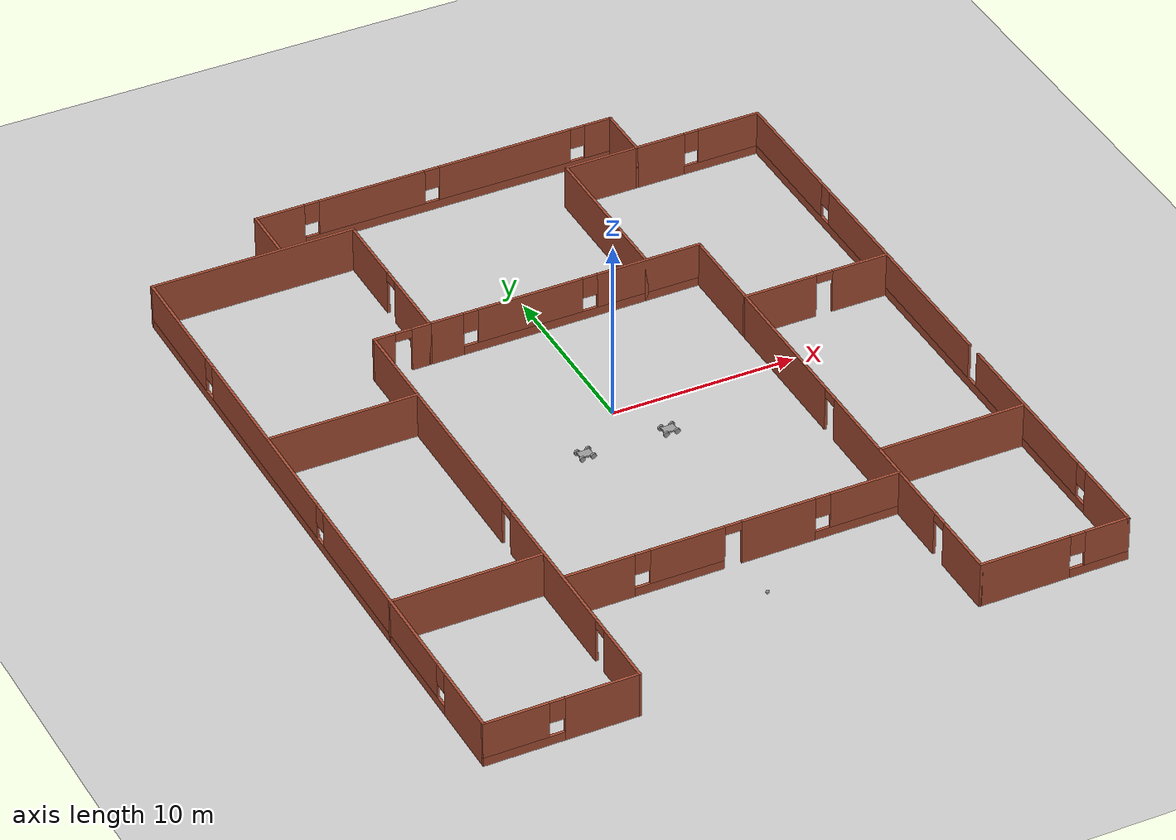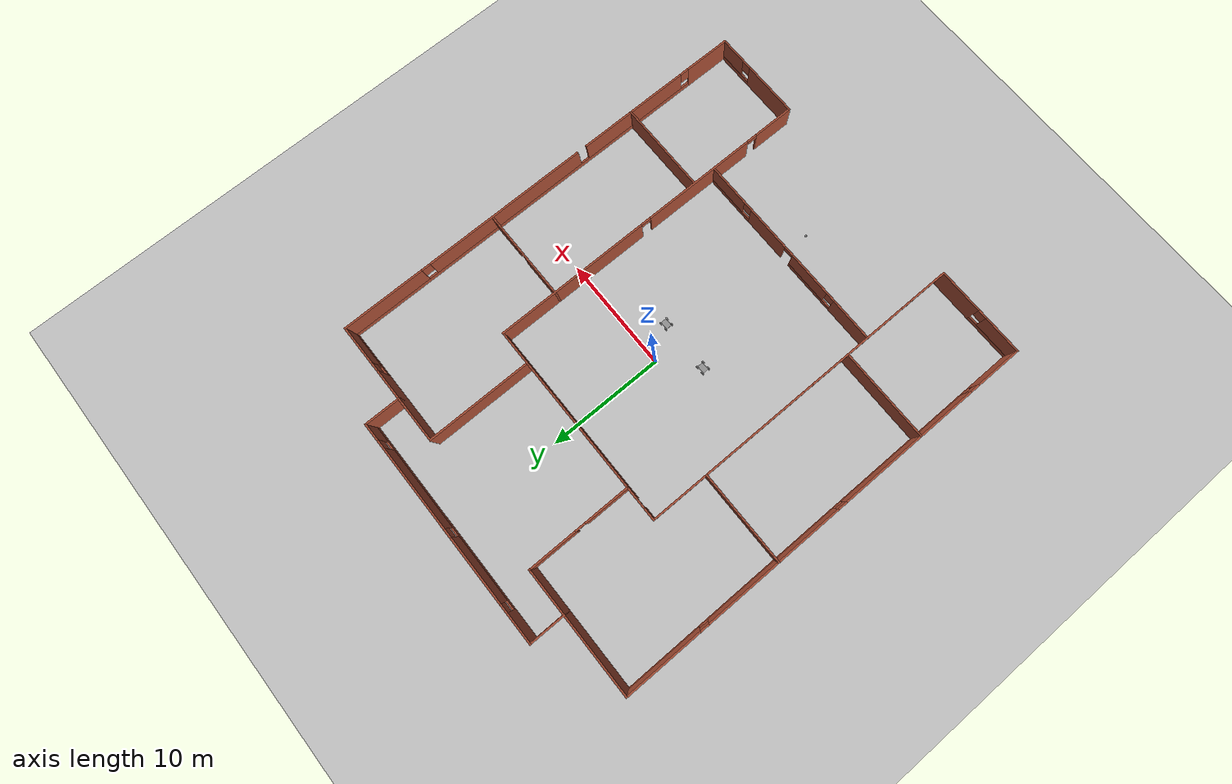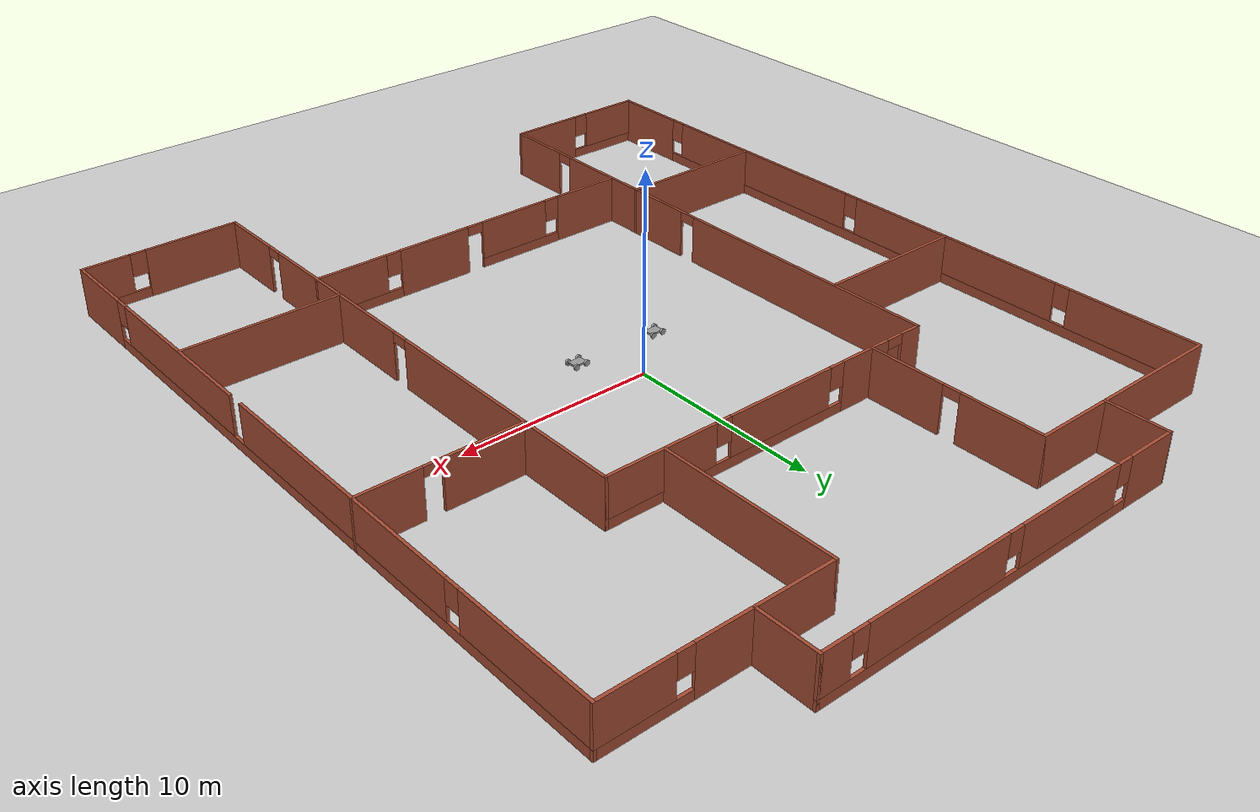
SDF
<sdf version="1.6">
 <world name="default">
  <plugin name="hello" filename="libhello.so"/>
  <light name="sun" type="directional">
   <pose>0 0 10 0 -0 0</pose>
   <diffuse>0.8 0.8 0.8 1</diffuse>
   <specular>0.2 0.2 0.2 1</specular>
   <attenuation>
    <range>1000</range>
    <constant>0.9</constant>
    <linear>0.01</linear>
    <quadratic>0.001</quadratic>
   </attenuation>
   <direction>-0.5 0.1 -0.9</direction>
  </light>
  <model name="ground_plane">
   <static>1</static>
   <link name="link">
    <collision name="collision">
     <geometry><plane><normal>0 0 1</normal><size>100 100</size></plane></geometry>
     <surface>
      <contact><collide_bitmask>65535</collide_bitmask></contact>
      <friction><ode><mu>100</mu><mu2>50</mu2></ode></friction>
     </surface>
    </collision>
    <visual name="visual">
     <cast_shadows>0</cast_shadows>
     <geometry><plane><normal>0 0 1</normal><size>100 100</size></plane></geometry>
     <material>
      <script><uri>file://media/materials/scripts/gazebo.material</uri><name>Gazebo/Grey</name></script>
     </material>
    </visual>
   </link>
  </model>
  <gravity>0 0 -9.8</gravity>
  <magnetic_field>6e-06 2.3e-05 -4.2e-05</magnetic_field>
  <atmosphere type="adiabatic"/>
  <physics name="default_physics" default="0" type="ode">
   <max_step_size>0.001</max_step_size>
   <real_time_factor>1</real_time_factor>
   <real_time_update_rate>1000</real_time_update_rate>
  </physics>
  <scene><ambient>0.4 0.4 0.4 1</ambient><background>0.7 0.7 0.7 1</background><shadows>1</shadows></scene>
  <spherical_coordinates>
   <surface_model>EARTH_WGS84</surface_model>
   <latitude_deg>0</latitude_deg>
   <longitude_deg>0</longitude_deg>
   <elevation>0</elevation>
   <heading_deg>0</heading_deg>
  </spherical_coordinates>
  <model name="structure">
   <pose>-0.2787 -0.7695 0 0 -0 0</pose>
   <link name="Wall_11">
    <collision name="Wall_11_Collision">
     <geometry><box><size>11.15 0.15 2.5</size></box></geometry>
     <pose>0 0 1.25 0 -0 0</pose>
    </collision>
    <visual name="Wall_11_Visual">
     <pose>0 0 1.25 0 -0 0</pose>
     <geometry><box><size>11.15 0.15 2.5</size></box></geometry>
     <material>
      <script><uri>file://media/materials/scripts/gazebo.material</uri><name>Gazebo/Bricks</name></script>
      <ambient>1 1 1 1</ambient>
     </material>
     <meta><layer>0</layer></meta>
    </visual>
    <pose>-11.5 17.5 0 0 -0 0</pose>
   </link>
   <link name="Wall_13">
    <pose>-6 13 0 0 0 -1.5708</pose>
    <visual name="Wall_13_Visual_0">
     <pose>-2.45369 0 1.25 0 -0 0</pose>
     <geometry><box><size>4.24262 0.15 2.5</size></box></geometry>
     <material>
      <script><uri>file://media/materials/scripts/gazebo.material</uri><name>Gazebo/Bricks</name></script>
      <ambient>1 1 1 1</ambient>
     </material>
     <meta><layer>0</layer></meta>
    </visual>
    <collision name="Wall_13_Collision_0">
     <geometry><box><size>4.24262 0.15 2.5</size></box></geometry>
     <pose>-2.45369 0 1.25 0 -0 0</pose>
    </collision>
    <visual name="Wall_13_Visual_1">
     <pose>2.57131 0 1.25 0 -0 0</pose>
     <geometry><box><size>4.00738 0.15 2.5</size></box></geometry>
     <material>
      <script><uri>file://media/materials/scripts/gazebo.material</uri><name>Gazebo/Bricks</name></script>
      <ambient>1 1 1 1</ambient>
     </material>
     <meta><layer>0</layer></meta>
    </visual>
    <collision name="Wall_13_Collision_1">
     <geometry><box><size>4.00738 0.15 2.5</size></box></geometry>
     <pose>2.57131 0 1.25 0 -0 0</pose>
    </collision>
    <visual name="Wall_13_Visual_2">
     <pose>0.117622 0 2.25 0 -0 0</pose>
     <geometry><box><size>0.9 0.15 0.5</size></box></geometry>
     <material>
      <script><uri>file://media/materials/scripts/gazebo.material</uri><name>Gazebo/Bricks</name></script>
      <ambient>1 1 1 1</ambient>
     </material>
     <meta><layer>0</layer></meta>
    </visual>
    <collision name="Wall_13_Collision_2">
     <geometry><box><size>0.9 0.15 0.5</size></box></geometry>
     <pose>0.117622 0 2.25 0 -0 0</pose>
    </collision>
   </link>
   <link name="Wall_15">
    <pose>-7.5 8.5 0 0 -0 3.14159</pose>
    <visual name="Wall_15_Visual_0">
     <pose>-1.03841 0 1.25 0 -0 0</pose>
     <geometry><box><size>1.07318 0.15 2.5</size></box></geometry>
     <material>
      <script><uri>file://media/materials/scripts/gazebo.material</uri><name>Gazebo/Bricks</name></script>
      <ambient>1 1 1 1</ambient>
     </material>
     <meta><layer>0</layer></meta>
    </visual>
    <collision name="Wall_15_Collision_0">
     <geometry><box><size>1.07318 0.15 2.5</size></box></geometry>
     <pose>-1.03841 0 1.25 0 -0 0</pose>
    </collision>
    <visual name="Wall_15_Visual_1">
     <pose>0.98659 0 1.25 0 -0 0</pose>
     <geometry><box><size>1.17682 0.15 2.5</size></box></geometry>
     <material>
      <script><uri>file://media/materials/scripts/gazebo.material</uri><name>Gazebo/Bricks</name></script>
      <ambient>1 1 1 1</ambient>
     </material>
     <meta><layer>0</layer></meta>
    </visual>
    <collision name="Wall_15_Collision_1">
     <geometry><box><size>1.17682 0.15 2.5</size></box></geometry>
     <pose>0.98659 0 1.25 0 -0 0</pose>
    </collision>
    <visual name="Wall_15_Visual_2">
     <pose>-0.051821 0 2.25 0 -0 0</pose>
     <geometry><box><size>0.9 0.15 0.5</size></box></geometry>
     <material>
      <script><uri>file://media/materials/scripts/gazebo.material</uri><name>Gazebo/Bricks</name></script>
      <ambient>1 1 1 1</ambient>
     </material>
     <meta><layer>0</layer></meta>
    </visual>
    <collision name="Wall_15_Collision_2">
     <geometry><box><size>0.9 0.15 0.5</size></box></geometry>
     <pose>-0.051821 0 2.25 0 -0 0</pose>
    </collision>
   </link>
   <link name="Wall_19">
    <pose>-9 -6 0 0 0 -1.5708</pose>
    <visual name="Wall_19_Visual_0">
     <pose>-7.2625 0 1.25 0 -0 0</pose>
     <geometry><box><size>14.625 0.15 2.5</size></box></geometry>
     <material>
      <script><uri>file://media/materials/scripts/gazebo.material</uri><name>Gazebo/Bricks</name></script>
      <ambient>1 1 1 1</ambient>
     </material>
     <meta><layer>0</layer></meta>
    </visual>
    <collision name="Wall_19_Collision_0">
     <geometry><box><size>14.625 0.15 2.5</size></box></geometry>
     <pose>-7.2625 0 1.25 0 -0 0</pose>
    </collision>
    <visual name="Wall_19_Visual_1">
     <pose>5.5 0 1.25 0 -0 0</pose>
     <geometry><box><size>9.1 0.15 2.5</size></box></geometry>
     <material>
      <script><uri>file://media/materials/scripts/gazebo.material</uri><name>Gazebo/Bricks</name></script>
      <ambient>1 1 1 1</ambient>
     </material>
     <meta><layer>0</layer></meta>
    </visual>
    <collision name="Wall_19_Collision_1">
     <geometry><box><size>9.1 0.15 2.5</size></box></geometry>
     <pose>5.5 0 1.25 0 -0 0</pose>
    </collision>
    <visual name="Wall_19_Visual_2">
     <pose>12.7625 0 1.25 0 -0 0</pose>
     <geometry><box><size>3.625 0.15 2.5</size></box></geometry>
     <material>
      <script><uri>file://media/materials/scripts/gazebo.material</uri><name>Gazebo/Bricks</name></script>
      <ambient>1 1 1 1</ambient>
     </material>
     <meta><layer>0</layer></meta>
    </visual>
    <collision name="Wall_19_Collision_2">
     <geometry><box><size>3.625 0.15 2.5</size></box></geometry>
     <pose>12.7625 0 1.25 0 -0 0</pose>
    </collision>
    <visual name="Wall_19_Visual_3">
     <pose>0.5 0 2.25 0 -0 0</pose>
     <geometry><box><size>0.9 0.15 0.5</size></box></geometry>
     <material>
      <script><uri>file://media/materials/scripts/gazebo.material</uri><name>Gazebo/Bricks</name></script>
      <ambient>1 1 1 1</ambient>
     </material>
     <meta><layer>0</layer></meta>
    </visual>
    <collision name="Wall_19_Collision_3">
     <geometry><box><size>0.9 0.15 0.5</size></box></geometry>
     <pose>0.5 0 2.25 0 -0 0</pose>
    </collision>
    <visual name="Wall_19_Visual_4">
     <pose>10.5 0 2.25 0 -0 0</pose>
     <geometry><box><size>0.9 0.15 0.5</size></box></geometry>
     <material>
      <script><uri>file://media/materials/scripts/gazebo.material</uri><name>Gazebo/Bricks</name></script>
      <ambient>1 1 1 1</ambient>
     </material>
     <meta><layer>0</layer></meta>
    </visual>
    <collision name="Wall_19_Collision_4">
     <geometry><box><size>0.9 0.15 0.5</size></box></geometry>
     <pose>10.5 0 2.25 0 -0 0</pose>
    </collision>
   </link>
   <link name="Wall_21">
    <pose>-13 -20.5 0 0 -0 3.14159</pose>
    <visual name="Wall_21_Visual_0">
     <pose>-2.10298 0 1.25 0 -0 0</pose>
     <geometry><box><size>3.94403 0.15 2.5</size></box></geometry>
     <material>
      <script><uri>file://media/materials/scripts/gazebo.material</uri><name>Gazebo/Bricks</name></script>
      <ambient>1 1 1 1</ambient>
     </material>
     <meta><layer>0</layer></meta>
    </visual>
    <collision name="Wall_21_Collision_0">
     <geometry><box><size>3.94403 0.15 2.5</size></box></geometry>
     <pose>-2.10298 0 1.25 0 -0 0</pose>
    </collision>
    <visual name="Wall_21_Visual_1">
     <pose>1.97202 0 0.25 0 -0 0</pose>
     <geometry><box><size>4.20597 0.15 0.5</size></box></geometry>
     <material>
      <script><uri>file://media/materials/scripts/gazebo.material</uri><name>Gazebo/Bricks</name></script>
      <ambient>1 1 1 1</ambient>
     </material>
     <meta><layer>0</layer></meta>
    </visual>
    <collision name="Wall_21_Collision_1">
     <geometry><box><size>4.20597 0.15 0.5</size></box></geometry>
     <pose>1.97202 0 0.25 0 -0 0</pose>
    </collision>
    <visual name="Wall_21_Visual_2">
     <pose>2.37202 0 1.5 0 -0 0</pose>
     <geometry><box><size>3.40597 0.15 2</size></box></geometry>
     <material>
      <script><uri>file://media/materials/scripts/gazebo.material</uri><name>Gazebo/Bricks</name></script>
      <ambient>1 1 1 1</ambient>
     </material>
     <meta><layer>0</layer></meta>
    </visual>
    <collision name="Wall_21_Collision_2">
     <geometry><box><size>3.40597 0.15 2</size></box></geometry>
     <pose>2.37202 0 1.5 0 -0 0</pose>
    </collision>
    <visual name="Wall_21_Visual_3">
     <pose>0.269032 0 1.9 0 -0 0</pose>
     <geometry><box><size>0.8 0.15 1.2</size></box></geometry>
     <material>
      <script><uri>file://media/materials/scripts/gazebo.material</uri><name>Gazebo/Bricks</name></script>
      <ambient>1 1 1 1</ambient>
     </material>
     <meta><layer>0</layer></meta>
    </visual>
    <collision name="Wall_21_Collision_3">
     <geometry><box><size>0.8 0.15 1.2</size></box></geometry>
     <pose>0.269032 0 1.9 0 -0 0</pose>
    </collision>
   </link>
   <link name="Wall_23">
    <collision name="Wall_23_Collision">
     <geometry><box><size>8.15 0.15 2.5</size></box></geometry>
     <pose>0 0 1.25 0 -0 0</pose>
    </collision>
    <visual name="Wall_23_Visual">
     <pose>0 0 1.25 0 -0 0</pose>
     <geometry><box><size>8.15 0.15 2.5</size></box></geometry>
     <material>
      <script><uri>file://media/materials/scripts/gazebo.material</uri><name>Gazebo/Bricks</name></script>
      <ambient>1 1 1 1</ambient>
     </material>
     <meta><layer>0</layer></meta>
    </visual>
    <pose>-13 3.5 0 0 -0 3.14159</pose>
   </link>
   <link name="Wall_25">
    <collision name="Wall_25_Collision">
     <geometry><box><size>8.15 0.15 2.5</size></box></geometry>
     <pose>0 0 1.25 0 -0 0</pose>
    </collision>
    <visual name="Wall_25_Visual">
     <pose>0 0 1.25 0 -0 0</pose>
     <geometry><box><size>8.15 0.15 2.5</size></box></geometry>
     <material>
      <script><uri>file://media/materials/scripts/gazebo.material</uri><name>Gazebo/Bricks</name></script>
      <ambient>0.921569 0.807843 0.615686 1</ambient>
     </material>
     <meta><layer>0</layer></meta>
    </visual>
    <pose>-13 -10.5 0 0 -0 3.14159</pose>
   </link>
   <link name="Wall_27">
    <pose>1e-06 -12.5 0 0 -0 0</pose>
    <visual name="Wall_27_Visual_0">
     <pose>-7.15272 0 1.25 0 -0 0</pose>
     <geometry><box><size>3.84455 0.15 2.5</size></box></geometry>
     <material>
      <script><uri>file://media/materials/scripts/gazebo.material</uri><name>Gazebo/Bricks</name></script>
      <ambient>0.921569 0.807843 0.615686 1</ambient>
     </material>
     <meta><layer>0</layer></meta>
    </visual>
    <collision name="Wall_27_Collision_0">
     <geometry><box><size>3.84455 0.15 2.5</size></box></geometry>
     <pose>-7.15272 0 1.25 0 -0 0</pose>
    </collision>
    <visual name="Wall_27_Visual_1">
     <pose>2.43616 0 1.25 0 -0 0</pose>
     <geometry><box><size>3.97232 0.15 2.5</size></box></geometry>
     <material>
      <script><uri>file://media/materials/scripts/gazebo.material</uri><name>Gazebo/Bricks</name></script>
      <ambient>0.921569 0.807843 0.615686 1</ambient>
     </material>
     <meta><layer>0</layer></meta>
    </visual>
    <collision name="Wall_27_Collision_1">
     <geometry><box><size>3.97232 0.15 2.5</size></box></geometry>
     <pose>2.43616 0 1.25 0 -0 0</pose>
    </collision>
    <visual name="Wall_27_Visual_2">
     <pose>-2.84022 0 0.25 0 -0 0</pose>
     <geometry><box><size>4.78045 0.15 0.5</size></box></geometry>
     <material>
      <script><uri>file://media/materials/scripts/gazebo.material</uri><name>Gazebo/Bricks</name></script>
      <ambient>0.921569 0.807843 0.615686 1</ambient>
     </material>
     <meta><layer>0</layer></meta>
    </visual>
    <collision name="Wall_27_Collision_2">
     <geometry><box><size>4.78045 0.15 0.5</size></box></geometry>
     <pose>-2.84022 0 0.25 0 -0 0</pose>
    </collision>
    <visual name="Wall_27_Visual_3">
     <pose>6.74866 0 0.25 0 -0 0</pose>
     <geometry><box><size>4.65268 0.15 0.5</size></box></geometry>
     <material>
      <script><uri>file://media/materials/scripts/gazebo.material</uri><name>Gazebo/Bricks</name></script>
      <ambient>0.921569 0.807843 0.615686 1</ambient>
     </material>
     <meta><layer>0</layer></meta>
    </visual>
    <collision name="Wall_27_Collision_3">
     <geometry><box><size>4.65268 0.15 0.5</size></box></geometry>
     <pose>6.74866 0 0.25 0 -0 0</pose>
    </collision>
    <visual name="Wall_27_Visual_4">
     <pose>-2.44022 0 1.5 0 -0 0</pose>
     <geometry><box><size>3.98045 0.15 2</size></box></geometry>
     <material>
      <script><uri>file://media/materials/scripts/gazebo.material</uri><name>Gazebo/Bricks</name></script>
      <ambient>0.921569 0.807843 0.615686 1</ambient>
     </material>
     <meta><layer>0</layer></meta>
    </visual>
    <collision name="Wall_27_Collision_4">
     <geometry><box><size>3.98045 0.15 2</size></box></geometry>
     <pose>-2.44022 0 1.5 0 -0 0</pose>
    </collision>
    <visual name="Wall_27_Visual_5">
     <pose>-2.44022 0 1.5 0 -0 0</pose>
     <geometry><box><size>3.98045 0.15 2</size></box></geometry>
     <material>
      <script><uri>file://media/materials/scripts/gazebo.material</uri><name>Gazebo/Bricks</name></script>
      <ambient>0.921569 0.807843 0.615686 1</ambient>
     </material>
     <meta><layer>0</layer></meta>
    </visual>
    <collision name="Wall_27_Collision_5">
     <geometry><box><size>3.98045 0.15 2</size></box></geometry>
     <pose>-2.44022 0 1.5 0 -0 0</pose>
    </collision>
    <visual name="Wall_27_Visual_6">
     <pose>7.14866 0 1.5 0 -0 0</pose>
     <geometry><box><size>3.85268 0.15 2</size></box></geometry>
     <material>
      <script><uri>file://media/materials/scripts/gazebo.material</uri><name>Gazebo/Bricks</name></script>
      <ambient>0.921569 0.807843 0.615686 1</ambient>
     </material>
     <meta><layer>0</layer></meta>
    </visual>
    <collision name="Wall_27_Collision_6">
     <geometry><box><size>3.85268 0.15 2</size></box></geometry>
     <pose>7.14866 0 1.5 0 -0 0</pose>
    </collision>
    <visual name="Wall_27_Visual_7">
     <pose>-4.83045 0 1.9 0 -0 0</pose>
     <geometry><box><size>0.8 0.15 1.2</size></box></geometry>
     <material>
      <script><uri>file://media/materials/scripts/gazebo.material</uri><name>Gazebo/Bricks</name></script>
      <ambient>0.921569 0.807843 0.615686 1</ambient>
     </material>
     <meta><layer>0</layer></meta>
    </visual>
    <collision name="Wall_27_Collision_7">
     <geometry><box><size>0.8 0.15 1.2</size></box></geometry>
     <pose>-4.83045 0 1.9 0 -0 0</pose>
    </collision>
    <visual name="Wall_27_Visual_8">
     <pose>4.82232 0 1.9 0 -0 0</pose>
     <geometry><box><size>0.8 0.15 1.2</size></box></geometry>
     <material>
      <script><uri>file://media/materials/scripts/gazebo.material</uri><name>Gazebo/Bricks</name></script>
      <ambient>0.921569 0.807843 0.615686 1</ambient>
     </material>
     <meta><layer>0</layer></meta>
    </visual>
    <collision name="Wall_27_Collision_8">
     <geometry><box><size>0.8 0.15 1.2</size></box></geometry>
     <pose>4.82232 0 1.9 0 -0 0</pose>
    </collision>
    <visual name="Wall_27_Visual_9">
     <pose>0 0 2.25 0 -0 0</pose>
     <geometry><box><size>0.9 0.15 0.5</size></box></geometry>
     <material>
      <script><uri>file://media/materials/scripts/gazebo.material</uri><name>Gazebo/Bricks</name></script>
      <ambient>0.921569 0.807843 0.615686 1</ambient>
     </material>
     <meta><layer>0</layer></meta>
    </visual>
    <collision name="Wall_27_Collision_9">
     <geometry><box><size>0.9 0.15 0.5</size></box></geometry>
     <pose>0 0 2.25 0 -0 0</pose>
    </collision>
    <visual name="Wall_27_Visual_10">
     <pose>0 0 2.25 0 -0 0</pose>
     <geometry><box><size>0.9 0.15 0.5</size></box></geometry>
     <material>
      <script><uri>file://media/materials/scripts/gazebo.material</uri><name>Gazebo/Bricks</name></script>
      <ambient>0.921569 0.807843 0.615686 1</ambient>
     </material>
     <meta><layer>0</layer></meta>
    </visual>
    <collision name="Wall_27_Collision_10">
     <geometry><box><size>0.9 0.15 0.5</size></box></geometry>
     <pose>0 0 2.25 0 -0 0</pose>
    </collision>
   </link>
   <link name="Wall_29">
    <pose>1.5 8.5 0 0 -0 0</pose>
    <visual name="Wall_29_Visual_0">
     <pose>-6.61866 0 1.25 0 -0 0</pose>
     <geometry><box><size>1.91268 0.15 2.5</size></box></geometry>
     <material>
      <script><uri>file://media/materials/scripts/gazebo.material</uri><name>Gazebo/Bricks</name></script>
      <ambient>1 1 1 1</ambient>
     </material>
     <meta><layer>0</layer></meta>
    </visual>
    <collision name="Wall_29_Collision_0">
     <geometry><box><size>1.91268 0.15 2.5</size></box></geometry>
     <pose>-6.61866 0 1.25 0 -0 0</pose>
    </collision>
    <visual name="Wall_29_Visual_1">
     <pose>0.956339 0 0.25 0 -0 0</pose>
     <geometry><box><size>13.2373 0.15 0.5</size></box></geometry>
     <material>
      <script><uri>file://media/materials/scripts/gazebo.material</uri><name>Gazebo/Bricks</name></script>
      <ambient>1 1 1 1</ambient>
     </material>
     <meta><layer>0</layer></meta>
    </visual>
    <collision name="Wall_29_Collision_1">
     <geometry><box><size>13.2373 0.15 0.5</size></box></geometry>
     <pose>0.956339 0 0.25 0 -0 0</pose>
    </collision>
    <visual name="Wall_29_Visual_2">
     <pose>-1.96235 0 1.5 0 -0 0</pose>
     <geometry><box><size>5.79994 0.15 2</size></box></geometry>
     <material>
      <script><uri>file://media/materials/scripts/gazebo.material</uri><name>Gazebo/Bricks</name></script>
      <ambient>1 1 1 1</ambient>
     </material>
     <meta><layer>0</layer></meta>
    </visual>
    <collision name="Wall_29_Collision_2">
     <geometry><box><size>5.79994 0.15 2</size></box></geometry>
     <pose>-1.96235 0 1.5 0 -0 0</pose>
    </collision>
    <visual name="Wall_29_Visual_3">
     <pose>4.65631 0 1.5 0 -0 0</pose>
     <geometry><box><size>5.83739 0.15 2</size></box></geometry>
     <material>
      <script><uri>file://media/materials/scripts/gazebo.material</uri><name>Gazebo/Bricks</name></script>
      <ambient>1 1 1 1</ambient>
     </material>
     <meta><layer>0</layer></meta>
    </visual>
    <collision name="Wall_29_Collision_3">
     <geometry><box><size>5.83739 0.15 2</size></box></geometry>
     <pose>4.65631 0 1.5 0 -0 0</pose>
    </collision>
    <visual name="Wall_29_Visual_4">
     <pose>-5.26232 0 1.9 0 -0 0</pose>
     <geometry><box><size>0.8 0.15 1.2</size></box></geometry>
     <material>
      <script><uri>file://media/materials/scripts/gazebo.material</uri><name>Gazebo/Bricks</name></script>
      <ambient>1 1 1 1</ambient>
     </material>
     <meta><layer>0</layer></meta>
    </visual>
    <collision name="Wall_29_Collision_4">
     <geometry><box><size>0.8 0.15 1.2</size></box></geometry>
     <pose>-5.26232 0 1.9 0 -0 0</pose>
    </collision>
    <visual name="Wall_29_Visual_5">
     <pose>1.33761 0 1.9 0 -0 0</pose>
     <geometry><box><size>0.8 0.15 1.2</size></box></geometry>
     <material>
      <script><uri>file://media/materials/scripts/gazebo.material</uri><name>Gazebo/Bricks</name></script>
      <ambient>1 1 1 1</ambient>
     </material>
     <meta><layer>0</layer></meta>
    </visual>
    <collision name="Wall_29_Collision_5">
     <geometry><box><size>0.8 0.15 1.2</size></box></geometry>
     <pose>1.33761 0 1.9 0 -0 0</pose>
    </collision>
   </link>
   <link name="Wall_31">
    <pose>9 -6 0 0 0 -1.5708</pose>
    <visual name="Wall_31_Visual_0">
     <pose>-7.7625 0 1.25 0 -0 0</pose>
     <geometry><box><size>13.625 0.15 2.5</size></box></geometry>
     <material>
      <script><uri>file://media/materials/scripts/gazebo.material</uri><name>Gazebo/Bricks</name></script>
      <ambient>1 1 1 1</ambient>
     </material>
     <meta><layer>0</layer></meta>
    </visual>
    <collision name="Wall_31_Collision_0">
     <geometry><box><size>13.625 0.15 2.5</size></box></geometry>
     <pose>-7.7625 0 1.25 0 -0 0</pose>
    </collision>
    <visual name="Wall_31_Visual_1">
     <pose>5 0 1.25 0 -0 0</pose>
     <geometry><box><size>10.1 0.15 2.5</size></box></geometry>
     <material>
      <script><uri>file://media/materials/scripts/gazebo.material</uri><name>Gazebo/Bricks</name></script>
      <ambient>1 1 1 1</ambient>
     </material>
     <meta><layer>0</layer></meta>
    </visual>
    <collision name="Wall_31_Collision_1">
     <geometry><box><size>10.1 0.15 2.5</size></box></geometry>
     <pose>5 0 1.25 0 -0 0</pose>
    </collision>
    <visual name="Wall_31_Visual_2">
     <pose>12.7625 0 1.25 0 -0 0</pose>
     <geometry><box><size>3.625 0.15 2.5</size></box></geometry>
     <material>
      <script><uri>file://media/materials/scripts/gazebo.material</uri><name>Gazebo/Bricks</name></script>
      <ambient>1 1 1 1</ambient>
     </material>
     <meta><layer>0</layer></meta>
    </visual>
    <collision name="Wall_31_Collision_2">
     <geometry><box><size>3.625 0.15 2.5</size></box></geometry>
     <pose>12.7625 0 1.25 0 -0 0</pose>
    </collision>
    <visual name="Wall_31_Visual_3">
     <pose>-0.5 0 2.25 0 -0 0</pose>
     <geometry><box><size>0.9 0.15 0.5</size></box></geometry>
     <material>
      <script><uri>file://media/materials/scripts/gazebo.material</uri><name>Gazebo/Bricks</name></script>
      <ambient>1 1 1 1</ambient>
     </material>
     <meta><layer>0</layer></meta>
    </visual>
    <collision name="Wall_31_Collision_3">
     <geometry><box><size>0.9 0.15 0.5</size></box></geometry>
     <pose>-0.5 0 2.25 0 -0 0</pose>
    </collision>
    <visual name="Wall_31_Visual_4">
     <pose>10.5 0 2.25 0 -0 0</pose>
     <geometry><box><size>0.9 0.15 0.5</size></box></geometry>
     <material>
      <script><uri>file://media/materials/scripts/gazebo.material</uri><name>Gazebo/Bricks</name></script>
      <ambient>1 1 1 1</ambient>
     </material>
     <meta><layer>0</layer></meta>
    </visual>
    <collision name="Wall_31_Collision_4">
     <geometry><box><size>0.9 0.15 0.5</size></box></geometry>
     <pose>10.5 0 2.25 0 -0 0</pose>
    </collision>
   </link>
   <link name="Wall_33">
    <pose>13 -20.5 0 0 -0 0</pose>
    <visual name="Wall_33_Visual_0">
     <pose>-1.62137 0 1.25 0 -0 0</pose>
     <geometry><box><size>4.90725 0.15 2.5</size></box></geometry>
     <material>
      <script><uri>file://media/materials/scripts/gazebo.material</uri><name>Gazebo/Bricks</name></script>
      <ambient>1 1 1 1</ambient>
     </material>
     <meta><layer>0</layer></meta>
    </visual>
    <collision name="Wall_33_Collision_0">
     <geometry><box><size>4.90725 0.15 2.5</size></box></geometry>
     <pose>-1.62137 0 1.25 0 -0 0</pose>
    </collision>
    <visual name="Wall_33_Visual_1">
     <pose>2.45363 0 0.25 0 -0 0</pose>
     <geometry><box><size>3.24275 0.15 0.5</size></box></geometry>
     <material>
      <script><uri>file://media/materials/scripts/gazebo.material</uri><name>Gazebo/Bricks</name></script>
      <ambient>1 1 1 1</ambient>
     </material>
     <meta><layer>0</layer></meta>
    </visual>
    <collision name="Wall_33_Collision_1">
     <geometry><box><size>3.24275 0.15 0.5</size></box></geometry>
     <pose>2.45363 0 0.25 0 -0 0</pose>
    </collision>
    <visual name="Wall_33_Visual_2">
     <pose>2.85363 0 1.5 0 -0 0</pose>
     <geometry><box><size>2.44275 0.15 2</size></box></geometry>
     <material>
      <script><uri>file://media/materials/scripts/gazebo.material</uri><name>Gazebo/Bricks</name></script>
      <ambient>1 1 1 1</ambient>
     </material>
     <meta><layer>0</layer></meta>
    </visual>
    <collision name="Wall_33_Collision_2">
     <geometry><box><size>2.44275 0.15 2</size></box></geometry>
     <pose>2.85363 0 1.5 0 -0 0</pose>
    </collision>
    <visual name="Wall_33_Visual_3">
     <pose>1.23225 0 1.9 0 -0 0</pose>
     <geometry><box><size>0.8 0.15 1.2</size></box></geometry>
     <material>
      <script><uri>file://media/materials/scripts/gazebo.material</uri><name>Gazebo/Bricks</name></script>
      <ambient>1 1 1 1</ambient>
     </material>
     <meta><layer>0</layer></meta>
    </visual>
    <collision name="Wall_33_Collision_3">
     <geometry><box><size>0.8 0.15 1.2</size></box></geometry>
     <pose>1.23225 0 1.9 0 -0 0</pose>
    </collision>
   </link>
   <link name="Wall_35">
    <pose>13 3.5 0 0 -0 0</pose>
    <visual name="Wall_35_Visual_0">
     <pose>-2.04491 0 1.25 0 -0 0</pose>
     <geometry><box><size>4.06018 0.15 2.5</size></box></geometry>
     <material>
      <script><uri>file://media/materials/scripts/gazebo.material</uri><name>Gazebo/Bricks</name></script>
      <ambient>1 1 1 1</ambient>
     </material>
     <meta><layer>0</layer></meta>
    </visual>
    <collision name="Wall_35_Collision_0">
     <geometry><box><size>4.06018 0.15 2.5</size></box></geometry>
     <pose>-2.04491 0 1.25 0 -0 0</pose>
    </collision>
    <visual name="Wall_35_Visual_1">
     <pose>2.48009 0 1.25 0 -0 0</pose>
     <geometry><box><size>3.18982 0.15 2.5</size></box></geometry>
     <material>
      <script><uri>file://media/materials/scripts/gazebo.material</uri><name>Gazebo/Bricks</name></script>
      <ambient>1 1 1 1</ambient>
     </material>
     <meta><layer>0</layer></meta>
    </visual>
    <collision name="Wall_35_Collision_1">
     <geometry><box><size>3.18982 0.15 2.5</size></box></geometry>
     <pose>2.48009 0 1.25 0 -0 0</pose>
    </collision>
    <visual name="Wall_35_Visual_2">
     <pose>0.435177 0 2.25 0 -0 0</pose>
     <geometry><box><size>0.9 0.15 0.5</size></box></geometry>
     <material>
      <script><uri>file://media/materials/scripts/gazebo.material</uri><name>Gazebo/Bricks</name></script>
      <ambient>1 1 1 1</ambient>
     </material>
     <meta><layer>0</layer></meta>
    </visual>
    <collision name="Wall_35_Collision_2">
     <geometry><box><size>0.9 0.15 0.5</size></box></geometry>
     <pose>0.435177 0 2.25 0 -0 0</pose>
    </collision>
   </link>
   <link name="Wall_37">
    <collision name="Wall_37_Collision">
     <geometry><box><size>8.15 0.15 2.5</size></box></geometry>
     <pose>0 0 1.25 0 -0 0</pose>
    </collision>
    <visual name="Wall_37_Visual">
     <pose>0 0 1.25 0 -0 0</pose>
     <geometry><box><size>8.15 0.15 2.5</size></box></geometry>
     <material>
      <script><uri>file://media/materials/scripts/gazebo.material</uri><name>Gazebo/Bricks</name></script>
      <ambient>1 1 1 1</ambient>
     </material>
     <meta><layer>0</layer></meta>
    </visual>
    <pose>13 -10.5 0 0 -0 0</pose>
   </link>
   <link name="Wall_39">
    <pose>17 -1.5 0 0 -0 1.5708</pose>
    <visual name="Wall_39_Visual_0">
     <pose>-17.0517 0 1.25 0 -0 0</pose>
     <geometry><box><size>4.04653 0.15 2.5</size></box></geometry>
     <material>
      <script><uri>file://media/materials/scripts/gazebo.material</uri><name>Gazebo/Bricks</name></script>
      <ambient>1 1 1 1</ambient>
     </material>
     <meta><layer>0</layer></meta>
    </visual>
    <collision name="Wall_39_Collision_0">
     <geometry><box><size>4.04653 0.15 2.5</size></box></geometry>
     <pose>-17.0517 0 1.25 0 -0 0</pose>
    </collision>
    <visual name="Wall_39_Visual_1">
     <pose>2.02327 0 0.25 0 -0 0</pose>
     <geometry><box><size>34.1035 0.15 0.5</size></box></geometry>
     <material>
      <script><uri>file://media/materials/scripts/gazebo.material</uri><name>Gazebo/Bricks</name></script>
      <ambient>1 1 1 1</ambient>
     </material>
     <meta><layer>0</layer></meta>
    </visual>
    <collision name="Wall_39_Collision_1">
     <geometry><box><size>34.1035 0.15 0.5</size></box></geometry>
     <pose>2.02327 0 0.25 0 -0 0</pose>
    </collision>
    <visual name="Wall_39_Visual_2">
     <pose>-9.28932 0 1.5 0 -0 0</pose>
     <geometry><box><size>9.8783 0.15 2</size></box></geometry>
     <material>
      <script><uri>file://media/materials/scripts/gazebo.material</uri><name>Gazebo/Bricks</name></script>
      <ambient>1 1 1 1</ambient>
     </material>
     <meta><layer>0</layer></meta>
    </visual>
    <collision name="Wall_39_Collision_2">
     <geometry><box><size>9.8783 0.15 2</size></box></geometry>
     <pose>-9.28932 0 1.5 0 -0 0</pose>
    </collision>
    <visual name="Wall_39_Visual_3">
     <pose>3.74165 0 1.5 0 -0 0</pose>
     <geometry><box><size>14.5836 0.15 2</size></box></geometry>
     <material>
      <script><uri>file://media/materials/scripts/gazebo.material</uri><name>Gazebo/Bricks</name></script>
      <ambient>1 1 1 1</ambient>
     </material>
     <meta><layer>0</layer></meta>
    </visual>
    <collision name="Wall_39_Collision_3">
     <geometry><box><size>14.5836 0.15 2</size></box></geometry>
     <pose>3.74165 0 1.5 0 -0 0</pose>
    </collision>
    <visual name="Wall_39_Visual_4">
     <pose>15.4542 0 1.5 0 -0 0</pose>
     <geometry><box><size>7.24153 0.15 2</size></box></geometry>
     <material>
      <script><uri>file://media/materials/scripts/gazebo.material</uri><name>Gazebo/Bricks</name></script>
      <ambient>1 1 1 1</ambient>
     </material>
     <meta><layer>0</layer></meta>
    </visual>
    <collision name="Wall_39_Collision_4">
     <geometry><box><size>7.24153 0.15 2</size></box></geometry>
     <pose>15.4542 0 1.5 0 -0 0</pose>
    </collision>
    <visual name="Wall_39_Visual_5">
     <pose>-14.6285 0 1.9 0 -0 0</pose>
     <geometry><box><size>0.8 0.15 1.2</size></box></geometry>
     <material>
      <script><uri>file://media/materials/scripts/gazebo.material</uri><name>Gazebo/Bricks</name></script>
      <ambient>1 1 1 1</ambient>
     </material>
     <meta><layer>0</layer></meta>
    </visual>
    <collision name="Wall_39_Collision_5">
     <geometry><box><size>0.8 0.15 1.2</size></box></geometry>
     <pose>-14.6285 0 1.9 0 -0 0</pose>
    </collision>
    <visual name="Wall_39_Visual_6">
     <pose>-4.35017 0 1.9 0 -0 0</pose>
     <geometry><box><size>0.0001 0.15 1.2</size></box></geometry>
     <material>
      <script><uri>file://media/materials/scripts/gazebo.material</uri><name>Gazebo/Bricks</name></script>
      <ambient>1 1 1 1</ambient>
     </material>
     <meta><layer>0</layer></meta>
    </visual>
    <collision name="Wall_39_Collision_6">
     <geometry><box><size>0.0001 0.15 1.2</size></box></geometry>
     <pose>-4.35017 0 1.9 0 -0 0</pose>
    </collision>
    <visual name="Wall_39_Visual_7">
     <pose>11.4335 0 1.9 0 -0 0</pose>
     <geometry><box><size>0.8 0.15 1.2</size></box></geometry>
     <material>
      <script><uri>file://media/materials/scripts/gazebo.material</uri><name>Gazebo/Bricks</name></script>
      <ambient>1 1 1 1</ambient>
     </material>
     <meta><layer>0</layer></meta>
    </visual>
    <collision name="Wall_39_Collision_7">
     <geometry><box><size>0.8 0.15 1.2</size></box></geometry>
     <pose>11.4335 0 1.9 0 -0 0</pose>
    </collision>
   </link>
   <link name="Wall_41">
    <collision name="Wall_41_Collision">
     <geometry><box><size>9.15 0.15 2.5</size></box></geometry>
     <pose>0 0 1.25 0 -0 0</pose>
    </collision>
    <visual name="Wall_41_Visual">
     <pose>0 0 1.25 0 -0 0</pose>
     <geometry><box><size>9.15 0.15 2.5</size></box></geometry>
     <material>
      <script><uri>file://media/materials/scripts/gazebo.material</uri><name>Gazebo/Bricks</name></script>
      <ambient>1 1 1 1</ambient>
     </material>
     <meta><layer>0</layer></meta>
    </visual>
    <pose>6 13 0 0 -0 1.5708</pose>
   </link>
   <link name="Wall_43">
    <pose>11.5 17.5 0 0 -0 0</pose>
    <visual name="Wall_43_Visual_0">
     <pose>-2.17048 0 1.25 0 -0 0</pose>
     <geometry><box><size>6.80905 0.15 2.5</size></box></geometry>
     <material>
      <script><uri>file://media/materials/scripts/gazebo.material</uri><name>Gazebo/Bricks</name></script>
      <ambient>1 1 1 1</ambient>
     </material>
     <meta><layer>0</layer></meta>
    </visual>
    <collision name="Wall_43_Collision_0">
     <geometry><box><size>6.80905 0.15 2.5</size></box></geometry>
     <pose>-2.17048 0 1.25 0 -0 0</pose>
    </collision>
    <visual name="Wall_43_Visual_1">
     <pose>3.40452 0 0.25 0 -0 0</pose>
     <geometry><box><size>4.34095 0.15 0.5</size></box></geometry>
     <material>
      <script><uri>file://media/materials/scripts/gazebo.material</uri><name>Gazebo/Bricks</name></script>
      <ambient>1 1 1 1</ambient>
     </material>
     <meta><layer>0</layer></meta>
    </visual>
    <collision name="Wall_43_Collision_1">
     <geometry><box><size>4.34095 0.15 0.5</size></box></geometry>
     <pose>3.40452 0 0.25 0 -0 0</pose>
    </collision>
    <visual name="Wall_43_Visual_2">
     <pose>3.80452 0 1.5 0 -0 0</pose>
     <geometry><box><size>3.54095 0.15 2</size></box></geometry>
     <material>
      <script><uri>file://media/materials/scripts/gazebo.material</uri><name>Gazebo/Bricks</name></script>
      <ambient>1 1 1 1</ambient>
     </material>
     <meta><layer>0</layer></meta>
    </visual>
    <collision name="Wall_43_Collision_2">
     <geometry><box><size>3.54095 0.15 2</size></box></geometry>
     <pose>3.80452 0 1.5 0 -0 0</pose>
    </collision>
    <visual name="Wall_43_Visual_3">
     <pose>1.63405 0 1.9 0 -0 0</pose>
     <geometry><box><size>0.8 0.15 1.2</size></box></geometry>
     <material>
      <script><uri>file://media/materials/scripts/gazebo.material</uri><name>Gazebo/Bricks</name></script>
      <ambient>1 1 1 1</ambient>
     </material>
     <meta><layer>0</layer></meta>
    </visual>
    <collision name="Wall_43_Collision_3">
     <geometry><box><size>0.8 0.15 1.2</size></box></geometry>
     <pose>1.63405 0 1.9 0 -0 0</pose>
    </collision>
   </link>
   <link name="Wall_45">
    <collision name="Wall_45_Collision">
     <geometry><box><size>3.15 0.15 2.5</size></box></geometry>
     <pose>0 0 1.25 0 -0 0</pose>
    </collision>
    <visual name="Wall_45_Visual">
     <pose>0 0 1.25 0 -0 0</pose>
     <geometry><box><size>3.15 0.15 2.5</size></box></geometry>
     <material>
      <script><uri>file://media/materials/scripts/gazebo.material</uri><name>Gazebo/Bricks</name></script>
      <ambient>1 1 1 1</ambient>
     </material>
     <meta><layer>0</layer></meta>
    </visual>
    <pose>-10 19 0 0 -0 1.5708</pose>
   </link>
   <link name="Wall_47">
    <collision name="Wall_47_Collision">
     <geometry><box><size>3.15 0.15 2.5</size></box></geometry>
     <pose>0 0 1.25 0 -0 0</pose>
    </collision>
    <visual name="Wall_47_Visual">
     <pose>0 0 1.25 0 -0 0</pose>
     <geometry><box><size>3.15 0.15 2.5</size></box></geometry>
     <material>
      <script><uri>file://media/materials/scripts/gazebo.material</uri><name>Gazebo/Bricks</name></script>
      <ambient>1 1 1 1</ambient>
     </material>
     <meta><layer>0</layer></meta>
    </visual>
    <pose>10 19 0 0 -0 1.5708</pose>
   </link>
   <link name="Wall_49">
    <pose>1e-06 20.5 0 0 -0 0</pose>
    <visual name="Wall_49_Visual_0">
     <pose>-8.7108 0 1.25 0 -0 0</pose>
     <geometry><box><size>2.72839 0.15 2.5</size></box></geometry>
     <material>
      <script><uri>file://media/materials/scripts/gazebo.material</uri><name>Gazebo/Bricks</name></script>
      <ambient>1 1 1 1</ambient>
     </material>
     <meta><layer>0</layer></meta>
    </visual>
    <collision name="Wall_49_Collision_0">
     <geometry><box><size>2.72839 0.15 2.5</size></box></geometry>
     <pose>-8.7108 0 1.25 0 -0 0</pose>
    </collision>
    <visual name="Wall_49_Visual_1">
     <pose>1.3642 0 0.25 0 -0 0</pose>
     <geometry><box><size>17.4216 0.15 0.5</size></box></geometry>
     <material>
      <script><uri>file://media/materials/scripts/gazebo.material</uri><name>Gazebo/Bricks</name></script>
      <ambient>1 1 1 1</ambient>
     </material>
     <meta><layer>0</layer></meta>
    </visual>
    <collision name="Wall_49_Collision_1">
     <geometry><box><size>17.4216 0.15 0.5</size></box></geometry>
     <pose>1.3642 0 0.25 0 -0 0</pose>
    </collision>
    <visual name="Wall_49_Visual_2">
     <pose>-3.57643 0 1.5 0 -0 0</pose>
     <geometry><box><size>5.94036 0.15 2</size></box></geometry>
     <material>
      <script><uri>file://media/materials/scripts/gazebo.material</uri><name>Gazebo/Bricks</name></script>
      <ambient>1 1 1 1</ambient>
     </material>
     <meta><layer>0</layer></meta>
    </visual>
    <collision name="Wall_49_Collision_2">
     <geometry><box><size>5.94036 0.15 2</size></box></geometry>
     <pose>-3.57643 0 1.5 0 -0 0</pose>
    </collision>
    <visual name="Wall_49_Visual_3">
     <pose>3.93627 0 1.5 0 -0 0</pose>
     <geometry><box><size>7.48503 0.15 2</size></box></geometry>
     <material>
      <script><uri>file://media/materials/scripts/gazebo.material</uri><name>Gazebo/Bricks</name></script>
      <ambient>1 1 1 1</ambient>
     </material>
     <meta><layer>0</layer></meta>
    </visual>
    <collision name="Wall_49_Collision_3">
     <geometry><box><size>7.48503 0.15 2</size></box></geometry>
     <pose>3.93627 0 1.5 0 -0 0</pose>
    </collision>
    <visual name="Wall_49_Visual_4">
     <pose>9.27689 0 1.5 0 -0 0</pose>
     <geometry><box><size>1.59622 0.15 2</size></box></geometry>
     <material>
      <script><uri>file://media/materials/scripts/gazebo.material</uri><name>Gazebo/Bricks</name></script>
      <ambient>1 1 1 1</ambient>
     </material>
     <meta><layer>0</layer></meta>
    </visual>
    <collision name="Wall_49_Collision_4">
     <geometry><box><size>1.59622 0.15 2</size></box></geometry>
     <pose>9.27689 0 1.5 0 -0 0</pose>
    </collision>
    <visual name="Wall_49_Visual_5">
     <pose>-6.94661 0 1.9 0 -0 0</pose>
     <geometry><box><size>0.8 0.15 1.2</size></box></geometry>
     <material>
      <script><uri>file://media/materials/scripts/gazebo.material</uri><name>Gazebo/Bricks</name></script>
      <ambient>1 1 1 1</ambient>
     </material>
     <meta><layer>0</layer></meta>
    </visual>
    <collision name="Wall_49_Collision_5">
     <geometry><box><size>0.8 0.15 1.2</size></box></geometry>
     <pose>-6.94661 0 1.9 0 -0 0</pose>
    </collision>
    <visual name="Wall_49_Visual_6">
     <pose>-0.206247 0 1.9 0 -0 0</pose>
     <geometry><box><size>0.8 0.15 1.2</size></box></geometry>
     <material>
      <script><uri>file://media/materials/scripts/gazebo.material</uri><name>Gazebo/Bricks</name></script>
      <ambient>1 1 1 1</ambient>
     </material>
     <meta><layer>0</layer></meta>
    </visual>
    <collision name="Wall_49_Collision_6">
     <geometry><box><size>0.8 0.15 1.2</size></box></geometry>
     <pose>-0.206247 0 1.9 0 -0 0</pose>
    </collision>
    <visual name="Wall_49_Visual_7">
     <pose>8.07878 0 1.9 0 -0 0</pose>
     <geometry><box><size>0.8 0.15 1.2</size></box></geometry>
     <material>
      <script><uri>file://media/materials/scripts/gazebo.material</uri><name>Gazebo/Bricks</name></script>
      <ambient>1 1 1 1</ambient>
     </material>
     <meta><layer>0</layer></meta>
    </visual>
    <collision name="Wall_49_Collision_7">
     <geometry><box><size>0.8 0.15 1.2</size></box></geometry>
     <pose>8.07878 0 1.9 0 -0 0</pose>
    </collision>
   </link>
   <link name="Wall_7">
    <pose>-17 -1.575 0 0 -0 1.5708</pose>
    <visual name="Wall_7_Visual_0">
     <pose>-16.9349 0 1.25 0 -0 0</pose>
     <geometry><box><size>4.13014 0.15 2.5</size></box></geometry>
     <material>
      <script><uri>file://media/materials/scripts/gazebo.material</uri><name>Gazebo/Bricks</name></script>
      <ambient>0.921569 0.807843 0.615686 1</ambient>
     </material>
     <meta><layer>0</layer></meta>
    </visual>
    <collision name="Wall_7_Collision_0">
     <geometry><box><size>4.13014 0.15 2.5</size></box></geometry>
     <pose>-16.9349 0 1.25 0 -0 0</pose>
    </collision>
    <visual name="Wall_7_Visual_1">
     <pose>2.06507 0 0.25 0 -0 0</pose>
     <geometry><box><size>33.8699 0.15 0.5</size></box></geometry>
     <material>
      <script><uri>file://media/materials/scripts/gazebo.material</uri><name>Gazebo/Bricks</name></script>
      <ambient>0.921569 0.807843 0.615686 1</ambient>
     </material>
     <meta><layer>0</layer></meta>
    </visual>
    <collision name="Wall_7_Collision_1">
     <geometry><box><size>33.8699 0.15 0.5</size></box></geometry>
     <pose>2.06507 0 0.25 0 -0 0</pose>
    </collision>
    <visual name="Wall_7_Visual_2">
     <pose>-7.77699 0 1.5 0 -0 0</pose>
     <geometry><box><size>12.5858 0.15 2</size></box></geometry>
     <material>
      <script><uri>file://media/materials/scripts/gazebo.material</uri><name>Gazebo/Bricks</name></script>
      <ambient>0.921569 0.807843 0.615686 1</ambient>
     </material>
     <meta><layer>0</layer></meta>
    </visual>
    <collision name="Wall_7_Collision_2">
     <geometry><box><size>12.5858 0.15 2</size></box></geometry>
     <pose>-7.77699 0 1.5 0 -0 0</pose>
    </collision>
    <visual name="Wall_7_Visual_3">
     <pose>5.45924 0 1.5 0 -0 0</pose>
     <geometry><box><size>12.2867 0.15 2</size></box></geometry>
     <material>
      <script><uri>file://media/materials/scripts/gazebo.material</uri><name>Gazebo/Bricks</name></script>
      <ambient>0.921569 0.807843 0.615686 1</ambient>
     </material>
     <meta><layer>0</layer></meta>
    </visual>
    <collision name="Wall_7_Collision_3">
     <geometry><box><size>12.2867 0.15 2</size></box></geometry>
     <pose>5.45924 0 1.5 0 -0 0</pose>
    </collision>
    <visual name="Wall_7_Visual_4">
     <pose>15.7013 0 1.5 0 -0 0</pose>
     <geometry><box><size>6.59741 0.15 2</size></box></geometry>
     <material>
      <script><uri>file://media/materials/scripts/gazebo.material</uri><name>Gazebo/Bricks</name></script>
      <ambient>0.921569 0.807843 0.615686 1</ambient>
     </material>
     <meta><layer>0</layer></meta>
    </visual>
    <collision name="Wall_7_Collision_4">
     <geometry><box><size>6.59741 0.15 2</size></box></geometry>
     <pose>15.7013 0 1.5 0 -0 0</pose>
    </collision>
    <visual name="Wall_7_Visual_5">
     <pose>-14.4699 0 1.9 0 -0 0</pose>
     <geometry><box><size>0.8 0.15 1.2</size></box></geometry>
     <material>
      <script><uri>file://media/materials/scripts/gazebo.material</uri><name>Gazebo/Bricks</name></script>
      <ambient>0.921569 0.807843 0.615686 1</ambient>
     </material>
     <meta><layer>0</layer></meta>
    </visual>
    <collision name="Wall_7_Collision_5">
     <geometry><box><size>0.8 0.15 1.2</size></box></geometry>
     <pose>-14.4699 0 1.9 0 -0 0</pose>
    </collision>
    <visual name="Wall_7_Visual_6">
     <pose>-1.08411 0 1.9 0 -0 0</pose>
     <geometry><box><size>0.8 0.15 1.2</size></box></geometry>
     <material>
      <script><uri>file://media/materials/scripts/gazebo.material</uri><name>Gazebo/Bricks</name></script>
      <ambient>0.921569 0.807843 0.615686 1</ambient>
     </material>
     <meta><layer>0</layer></meta>
    </visual>
    <collision name="Wall_7_Collision_6">
     <geometry><box><size>0.8 0.15 1.2</size></box></geometry>
     <pose>-1.08411 0 1.9 0 -0 0</pose>
    </collision>
    <visual name="Wall_7_Visual_7">
     <pose>12.0026 0 1.9 0 -0 0</pose>
     <geometry><box><size>0.8 0.15 1.2</size></box></geometry>
     <material>
      <script><uri>file://media/materials/scripts/gazebo.material</uri><name>Gazebo/Bricks</name></script>
      <ambient>0.921569 0.807843 0.615686 1</ambient>
     </material>
     <meta><layer>0</layer></meta>
    </visual>
    <collision name="Wall_7_Collision_7">
     <geometry><box><size>0.8 0.15 1.2</size></box></geometry>
     <pose>12.0026 0 1.9 0 -0 0</pose>
    </collision>
   </link>
   <static>1</static>
  </model>
  <model name="bot">
   <link name="link_0">
    <pose>0 0 0.008004 0 -0 0</pose>
    <inertial>
     <mass>1</mass>
     <inertia>
      <ixx>0.166667</ixx>
      <ixy>0</ixy>
      <ixz>0</ixz>
      <iyy>0.166667</iyy>
      <iyz>0</iyz>
      <izz>0.166667</izz>
     </inertia>
    </inertial>
    <visual name="visual">
     <geometry><box><size>0.7 0.5 0.1</size></box></geometry>
     <material>
      <lighting>1</lighting>
      <script><uri>file://media/materials/scripts/gazebo.material</uri><name>Gazebo/Grey</name></script>
      <shader type="pixel"><normal_map>__default__</normal_map></shader>
      <ambient>0.3 0.3 0.3 1</ambient>
      <diffuse>0.7 0.7 0.7 1</diffuse>
      <specular>0.01 0.01 0.01 1</specular>
      <emissive>0 0 0 1</emissive>
     </material>
    </visual>
    <collision name="collision">
     <geometry><box><size>0.7 0.5 0.1</size></box></geometry>
     <surface>
      <friction>
       <ode><mu>1</mu><mu2>1</mu2><fdir1>0 0 0</fdir1><slip1>0</slip1><slip2>0</slip2></ode>
       <torsional>
        <coefficient>1</coefficient>
        <patch_radius>0</patch_radius>
        <surface_radius>0</surface_radius>
        <use_patch_radius>1</use_patch_radius>
        <ode><slip>0</slip></ode>
       </torsional>
      </friction>
      <bounce><restitution_coefficient>0</restitution_coefficient><threshold>1e+06</threshold></bounce>
      <contact>
       <collide_without_contact>0</collide_without_contact>
       <collide_without_contact_bitmask>1</collide_without_contact_bitmask>
       <collide_bitmask>1</collide_bitmask>
       <ode>
        <soft_cfm>0</soft_cfm>
        <soft_erp>0.2</soft_erp>
        <kp>1e+13</kp>
        <kd>1</kd>
        <max_vel>0.01</max_vel>
        <min_depth>0</min_depth>
       </ode>
       <bullet>
        <split_impulse>1</split_impulse>
        <split_impulse_penetration_threshold>-0.01</split_impulse_penetration_threshold>
        <soft_cfm>0</soft_cfm>
        <soft_erp>0.2</soft_erp>
        <kp>1e+13</kp>
        <kd>1</kd>
       </bullet>
      </contact>
     </surface>
    </collision>
   </link>
   <link name="link_1_clone">
    <pose>-0.3 0.300014 -0.002001 0 -0 0</pose>
    <inertial>
     <mass>1</mass>
     <inertia><ixx>0.145833</ixx><ixy>0</ixy><ixz>0</ixz><iyy>0.145833</iyy><iyz>0</iyz><izz>0.125</izz></inertia>
    </inertial>
    <visual name="visual">
     <pose>0 0 0 1.5707 -0 0</pose>
     <geometry><cylinder><radius>0.15</radius><length>0.1</length></cylinder></geometry>
     <material>
      <lighting>1</lighting>
      <script><uri>file://media/materials/scripts/gazebo.material</uri><name>Gazebo/Grey</name></script>
      <shader type="pixel"><normal_map>__default__</normal_map></shader>
      <ambient>0.3 0.3 0.3 1</ambient>
      <diffuse>0.7 0.7 0.7 1</diffuse>
      <specular>0.01 0.01 0.01 1</specular>
      <emissive>0 0 0 1</emissive>
     </material>
    </visual>
    <collision name="collision">
     <pose>0 0 0 1.5707 -0 0</pose>
     <geometry><cylinder><radius>0.15</radius><length>0.1</length></cylinder></geometry>
     <surface>
      <friction>
       <ode><mu>1</mu><mu2>1</mu2><fdir1>0 0 0</fdir1><slip1>0</slip1><slip2>0</slip2></ode>
       <torsional>
        <coefficient>1</coefficient>
        <patch_radius>0</patch_radius>
        <surface_radius>0</surface_radius>
        <use_patch_radius>1</use_patch_radius>
        <ode><slip>0</slip></ode>
       </torsional>
      </friction>
      <bounce><restitution_coefficient>0</restitution_coefficient><threshold>1e+06</threshold></bounce>
      <contact>
       <collide_without_contact>0</collide_without_contact>
       <collide_without_contact_bitmask>1</collide_without_contact_bitmask>
       <collide_bitmask>1</collide_bitmask>
       <ode>
        <soft_cfm>0</soft_cfm>
        <soft_erp>0.2</soft_erp>
        <kp>1e+13</kp>
        <kd>1</kd>
        <max_vel>0.01</max_vel>
        <min_depth>0</min_depth>
       </ode>
       <bullet>
        <split_impulse>1</split_impulse>
        <split_impulse_penetration_threshold>-0.01</split_impulse_penetration_threshold>
        <soft_cfm>0</soft_cfm>
        <soft_erp>0.2</soft_erp>
        <kp>1e+13</kp>
        <kd>1</kd>
       </bullet>
      </contact>
     </surface>
    </collision>
   </link>
   <link name="link_1_clone_0">
    <pose>0.3 0.300014 -0.002001 0 -0 0</pose>
    <inertial>
     <mass>1</mass>
     <inertia><ixx>0.145833</ixx><ixy>0</ixy><ixz>0</ixz><iyy>0.145833</iyy><iyz>0</iyz><izz>0.125</izz></inertia>
    </inertial>
    <visual name="visual">
     <pose>0 0 0 1.5707 -0 0</pose>
     <geometry><cylinder><radius>0.15</radius><length>0.1</length></cylinder></geometry>
     <material>
      <lighting>1</lighting>
      <script><uri>file://media/materials/scripts/gazebo.material</uri><name>Gazebo/Grey</name></script>
      <shader type="pixel"><normal_map>__default__</normal_map></shader>
      <ambient>0.3 0.3 0.3 1</ambient>
      <diffuse>0.7 0.7 0.7 1</diffuse>
      <specular>0.01 0.01 0.01 1</specular>
      <emissive>0 0 0 1</emissive>
     </material>
    </visual>
    <collision name="collision">
     <pose>0 0 0 1.5707 -0 0</pose>
     <geometry><cylinder><radius>0.15</radius><length>0.1</length></cylinder></geometry>
     <surface>
      <friction>
       <ode><mu>1</mu><mu2>1</mu2><fdir1>0 0 0</fdir1><slip1>0</slip1><slip2>0</slip2></ode>
       <torsional>
        <coefficient>1</coefficient>
        <patch_radius>0</patch_radius>
        <surface_radius>0</surface_radius>
        <use_patch_radius>1</use_patch_radius>
        <ode><slip>0</slip></ode>
       </torsional>
      </friction>
      <bounce><restitution_coefficient>0</restitution_coefficient><threshold>1e+06</threshold></bounce>
      <contact>
       <collide_without_contact>0</collide_without_contact>
       <collide_without_contact_bitmask>1</collide_without_contact_bitmask>
       <collide_bitmask>1</collide_bitmask>
       <ode>
        <soft_cfm>0</soft_cfm>
        <soft_erp>0.2</soft_erp>
        <kp>1e+13</kp>
        <kd>1</kd>
        <max_vel>0.01</max_vel>
        <min_depth>0</min_depth>
       </ode>
       <bullet>
        <split_impulse>1</split_impulse>
        <split_impulse_penetration_threshold>-0.01</split_impulse_penetration_threshold>
        <soft_cfm>0</soft_cfm>
        <soft_erp>0.2</soft_erp>
        <kp>1e+13</kp>
        <kd>1</kd>
       </bullet>
      </contact>
     </surface>
    </collision>
   </link>
   <link name="link_1_clone_1">
    <pose>0.3 -0.300014 -0.002001 0 -0 0</pose>
    <inertial>
     <mass>1</mass>
     <inertia><ixx>0.145833</ixx><ixy>0</ixy><ixz>0</ixz><iyy>0.145833</iyy><iyz>0</iyz><izz>0.125</izz></inertia>
    </inertial>
    <visual name="visual">
     <pose>0 0 0 1.5707 -0 0</pose>
     <geometry><cylinder><radius>0.15</radius><length>0.1</length></cylinder></geometry>
     <material>
      <lighting>1</lighting>
      <script><uri>file://media/materials/scripts/gazebo.material</uri><name>Gazebo/Grey</name></script>
      <shader type="pixel"><normal_map>__default__</normal_map></shader>
      <ambient>0.3 0.3 0.3 1</ambient>
      <diffuse>0.7 0.7 0.7 1</diffuse>
      <specular>0.01 0.01 0.01 1</specular>
      <emissive>0 0 0 1</emissive>
     </material>
    </visual>
    <collision name="collision">
     <pose>0 0 0 1.5707 -0 0</pose>
     <geometry><cylinder><radius>0.15</radius><length>0.1</length></cylinder></geometry>
     <surface>
      <friction>
       <ode><mu>1</mu><mu2>1</mu2><fdir1>0 0 0</fdir1><slip1>0</slip1><slip2>0</slip2></ode>
       <torsional>
        <coefficient>1</coefficient>
        <patch_radius>0</patch_radius>
        <surface_radius>0</surface_radius>
        <use_patch_radius>1</use_patch_radius>
        <ode><slip>0</slip></ode>
       </torsional>
      </friction>
      <bounce><restitution_coefficient>0</restitution_coefficient><threshold>1e+06</threshold></bounce>
      <contact>
       <collide_without_contact>0</collide_without_contact>
       <collide_without_contact_bitmask>1</collide_without_contact_bitmask>
       <collide_bitmask>1</collide_bitmask>
       <ode>
        <soft_cfm>0</soft_cfm>
        <soft_erp>0.2</soft_erp>
        <kp>1e+13</kp>
        <kd>1</kd>
        <max_vel>0.01</max_vel>
        <min_depth>0</min_depth>
       </ode>
       <bullet>
        <split_impulse>1</split_impulse>
        <split_impulse_penetration_threshold>-0.01</split_impulse_penetration_threshold>
        <soft_cfm>0</soft_cfm>
        <soft_erp>0.2</soft_erp>
        <kp>1e+13</kp>
        <kd>1</kd>
       </bullet>
      </contact>
     </surface>
    </collision>
   </link>
   <link name="link_1_clone_2">
    <pose>-0.3 -0.300014 -0.002001 0 -0 0</pose>
    <inertial>
     <mass>1</mass>
     <inertia><ixx>0.145833</ixx><ixy>0</ixy><ixz>0</ixz><iyy>0.145833</iyy><iyz>0</iyz><izz>0.125</izz></inertia>
    </inertial>
    <visual name="visual">
     <pose>0 0 0 1.5707 -0 0</pose>
     <geometry><cylinder><radius>0.15</radius><length>0.1</length></cylinder></geometry>
     <material>
      <lighting>1</lighting>
      <script><uri>file://media/materials/scripts/gazebo.material</uri><name>Gazebo/Grey</name></script>
      <shader type="pixel"><normal_map>__default__</normal_map></shader>
      <ambient>0.3 0.3 0.3 1</ambient>
      <diffuse>0.7 0.7 0.7 1</diffuse>
      <specular>0.01 0.01 0.01 1</specular>
      <emissive>0 0 0 1</emissive>
     </material>
    </visual>
    <collision name="collision">
     <pose>0 0 0 1.5707 -0 0</pose>
     <geometry><cylinder><radius>0.15</radius><length>0.1</length></cylinder></geometry>
     <surface>
      <friction>
       <ode><mu>1</mu><mu2>1</mu2><fdir1>0 0 0</fdir1><slip1>0</slip1><slip2>0</slip2></ode>
       <torsional>
        <coefficient>1</coefficient>
        <patch_radius>0</patch_radius>
        <surface_radius>0</surface_radius>
        <use_patch_radius>1</use_patch_radius>
        <ode><slip>0</slip></ode>
       </torsional>
      </friction>
      <bounce><restitution_coefficient>0</restitution_coefficient><threshold>1e+06</threshold></bounce>
      <contact>
       <collide_without_contact>0</collide_without_contact>
       <collide_without_contact_bitmask>1</collide_without_contact_bitmask>
       <collide_bitmask>1</collide_bitmask>
       <ode>
        <soft_cfm>0</soft_cfm>
        <soft_erp>0.2</soft_erp>
        <kp>1e+13</kp>
        <kd>1</kd>
        <max_vel>0.01</max_vel>
        <min_depth>0</min_depth>
       </ode>
       <bullet>
        <split_impulse>1</split_impulse>
        <split_impulse_penetration_threshold>-0.01</split_impulse_penetration_threshold>
        <soft_cfm>0</soft_cfm>
        <soft_erp>0.2</soft_erp>
        <kp>1e+13</kp>
        <kd>1</kd>
       </bullet>
      </contact>
     </surface>
    </collision>
   </link>
   <joint name="link_0_JOINT_1" type="revolute">
    <parent>link_0</parent>
    <child>link_1_clone</child>
    <axis>
     <xyz>0 1 0</xyz>
     <use_parent_model_frame>0</use_parent_model_frame>
     <limit>
      <lower>-1.79769e+308</lower>
      <upper>1.79769e+308</upper>
      <effort>-1</effort>
      <velocity>-1</velocity>
     </limit>
     <dynamics>
      <spring_reference>0</spring_reference>
      <spring_stiffness>0</spring_stiffness>
      <damping>0</damping>
     </dynamics>
    </axis>
    <physics>
     <ode><limit><cfm>0</cfm><erp>0.2</erp></limit><suspension><cfm>0</cfm><erp>0.2</erp></suspension></ode>
    </physics>
   </joint>
   <joint name="link_0_JOINT_2" type="revolute">
    <parent>link_0</parent>
    <child>link_1_clone_0</child>
    <axis>
     <xyz>0 1 0</xyz>
     <use_parent_model_frame>0</use_parent_model_frame>
     <limit>
      <lower>-1.79769e+308</lower>
      <upper>1.79769e+308</upper>
      <effort>-1</effort>
      <velocity>-1</velocity>
     </limit>
     <dynamics>
      <spring_reference>0</spring_reference>
      <spring_stiffness>0</spring_stiffness>
      <damping>0</damping>
     </dynamics>
    </axis>
    <physics>
     <ode><limit><cfm>0</cfm><erp>0.2</erp></limit><suspension><cfm>0</cfm><erp>0.2</erp></suspension></ode>
    </physics>
   </joint>
   <joint name="link_0_JOINT_3" type="revolute">
    <parent>link_0</parent>
    <child>link_1_clone_1</child>
    <axis>
     <xyz>0 -1 0</xyz>
     <use_parent_model_frame>0</use_parent_model_frame>
     <limit>
      <lower>-1.79769e+308</lower>
      <upper>1.79769e+308</upper>
      <effort>-1</effort>
      <velocity>-1</velocity>
     </limit>
     <dynamics>
      <spring_reference>0</spring_reference>
      <spring_stiffness>0</spring_stiffness>
      <damping>0</damping>
     </dynamics>
    </axis>
    <physics>
     <ode><limit><cfm>0</cfm><erp>0.2</erp></limit><suspension><cfm>0</cfm><erp>0.2</erp></suspension></ode>
    </physics>
   </joint>
   <joint name="link_0_JOINT_4" type="revolute">
    <parent>link_0</parent>
    <child>link_1_clone_2</child>
    <axis>
     <xyz>0 -1 0</xyz>
     <use_parent_model_frame>0</use_parent_model_frame>
     <limit>
      <lower>-1.79769e+308</lower>
      <upper>1.79769e+308</upper>
      <effort>-1</effort>
      <velocity>-1</velocity>
     </limit>
     <dynamics>
      <spring_reference>0</spring_reference>
      <spring_stiffness>0</spring_stiffness>
      <damping>0</damping>
     </dynamics>
    </axis>
    <physics>
     <ode><limit><cfm>0</cfm><erp>0.2</erp></limit><suspension><cfm>0</cfm><erp>0.2</erp></suspension></ode>
    </physics>
   </joint>
   <static>0</static>
   <pose>-2.77247 -2.50005 0.152002 -8e-06 7e-06 0.01559</pose>
  </model>
  <model name="bot_0">
   <link name="link_0">
    <pose>0 0 0.008004 0 -0 0</pose>
    <inertial>
     <mass>1</mass>
     <inertia>
      <ixx>0.166667</ixx>
      <ixy>0</ixy>
      <ixz>0</ixz>
      <iyy>0.166667</iyy>
      <iyz>0</iyz>
      <izz>0.166667</izz>
     </inertia>
    </inertial>
    <visual name="visual">
     <geometry><box><size>0.7 0.5 0.1</size></box></geometry>
     <material>
      <lighting>1</lighting>
      <script><uri>file://media/materials/scripts/gazebo.material</uri><name>Gazebo/Grey</name></script>
      <shader type="pixel"><normal_map>__default__</normal_map></shader>
      <ambient>0.3 0.3 0.3 1</ambient>
      <diffuse>0.7 0.7 0.7 1</diffuse>
      <specular>0.01 0.01 0.01 1</specular>
      <emissive>0 0 0 1</emissive>
     </material>
    </visual>
    <collision name="collision">
     <geometry><box><size>0.7 0.5 0.1</size></box></geometry>
     <surface>
      <friction>
       <ode><mu>1</mu><mu2>1</mu2><fdir1>0 0 0</fdir1><slip1>0</slip1><slip2>0</slip2></ode>
       <torsional>
        <coefficient>1</coefficient>
        <patch_radius>0</patch_radius>
        <surface_radius>0</surface_radius>
        <use_patch_radius>1</use_patch_radius>
        <ode><slip>0</slip></ode>
       </torsional>
      </friction>
      <bounce><restitution_coefficient>0</restitution_coefficient><threshold>1e+06</threshold></bounce>
      <contact>
       <collide_without_contact>0</collide_without_contact>
       <collide_without_contact_bitmask>1</collide_without_contact_bitmask>
       <collide_bitmask>1</collide_bitmask>
       <ode>
        <soft_cfm>0</soft_cfm>
        <soft_erp>0.2</soft_erp>
        <kp>1e+13</kp>
        <kd>1</kd>
        <max_vel>0.01</max_vel>
        <min_depth>0</min_depth>
       </ode>
       <bullet>
        <split_impulse>1</split_impulse>
        <split_impulse_penetration_threshold>-0.01</split_impulse_penetration_threshold>
        <soft_cfm>0</soft_cfm>
        <soft_erp>0.2</soft_erp>
        <kp>1e+13</kp>
        <kd>1</kd>
       </bullet>
      </contact>
     </surface>
    </collision>
   </link>
   <link name="link_1_clone">
    <pose>-0.3 0.300014 -0.002001 0 -0 0</pose>
    <inertial>
     <mass>1</mass>
     <inertia><ixx>0.145833</ixx><ixy>0</ixy><ixz>0</ixz><iyy>0.145833</iyy><iyz>0</iyz><izz>0.125</izz></inertia>
    </inertial>
    <visual name="visual">
     <pose>0 0 0 1.5707 -0 0</pose>
     <geometry><cylinder><radius>0.15</radius><length>0.1</length></cylinder></geometry>
     <material>
      <lighting>1</lighting>
      <script><uri>file://media/materials/scripts/gazebo.material</uri><name>Gazebo/Grey</name></script>
      <shader type="pixel"><normal_map>__default__</normal_map></shader>
      <ambient>0.3 0.3 0.3 1</ambient>
      <diffuse>0.7 0.7 0.7 1</diffuse>
      <specular>0.01 0.01 0.01 1</specular>
      <emissive>0 0 0 1</emissive>
     </material>
    </visual>
    <collision name="collision">
     <pose>0 0 0 1.5707 -0 0</pose>
     <geometry><cylinder><radius>0.15</radius><length>0.1</length></cylinder></geometry>
     <surface>
      <friction>
       <ode><mu>1</mu><mu2>1</mu2><fdir1>0 0 0</fdir1><slip1>0</slip1><slip2>0</slip2></ode>
       <torsional>
        <coefficient>1</coefficient>
        <patch_radius>0</patch_radius>
        <surface_radius>0</surface_radius>
        <use_patch_radius>1</use_patch_radius>
        <ode><slip>0</slip></ode>
       </torsional>
      </friction>
      <bounce><restitution_coefficient>0</restitution_coefficient><threshold>1e+06</threshold></bounce>
      <contact>
       <collide_without_contact>0</collide_without_contact>
       <collide_without_contact_bitmask>1</collide_without_contact_bitmask>
       <collide_bitmask>1</collide_bitmask>
       <ode>
        <soft_cfm>0</soft_cfm>
        <soft_erp>0.2</soft_erp>
        <kp>1e+13</kp>
        <kd>1</kd>
        <max_vel>0.01</max_vel>
        <min_depth>0</min_depth>
       </ode>
       <bullet>
        <split_impulse>1</split_impulse>
        <split_impulse_penetration_threshold>-0.01</split_impulse_penetration_threshold>
        <soft_cfm>0</soft_cfm>
        <soft_erp>0.2</soft_erp>
        <kp>1e+13</kp>
        <kd>1</kd>
       </bullet>
      </contact>
     </surface>
    </collision>
   </link>
   <link name="link_1_clone_0">
    <pose>0.3 0.300014 -0.002001 0 -0 0</pose>
    <inertial>
     <mass>1</mass>
     <inertia><ixx>0.145833</ixx><ixy>0</ixy><ixz>0</ixz><iyy>0.145833</iyy><iyz>0</iyz><izz>0.125</izz></inertia>
    </inertial>
    <visual name="visual">
     <pose>0 0 0 1.5707 -0 0</pose>
     <geometry><cylinder><radius>0.15</radius><length>0.1</length></cylinder></geometry>
     <material>
      <lighting>1</lighting>
      <script><uri>file://media/materials/scripts/gazebo.material</uri><name>Gazebo/Grey</name></script>
      <shader type="pixel"><normal_map>__default__</normal_map></shader>
      <ambient>0.3 0.3 0.3 1</ambient>
      <diffuse>0.7 0.7 0.7 1</diffuse>
      <specular>0.01 0.01 0.01 1</specular>
      <emissive>0 0 0 1</emissive>
     </material>
    </visual>
    <collision name="collision">
     <pose>0 0 0 1.5707 -0 0</pose>
     <geometry><cylinder><radius>0.15</radius><length>0.1</length></cylinder></geometry>
     <surface>
      <friction>
       <ode><mu>1</mu><mu2>1</mu2><fdir1>0 0 0</fdir1><slip1>0</slip1><slip2>0</slip2></ode>
       <torsional>
        <coefficient>1</coefficient>
        <patch_radius>0</patch_radius>
        <surface_radius>0</surface_radius>
        <use_patch_radius>1</use_patch_radius>
        <ode><slip>0</slip></ode>
       </torsional>
      </friction>
      <bounce><restitution_coefficient>0</restitution_coefficient><threshold>1e+06</threshold></bounce>
      <contact>
       <collide_without_contact>0</collide_without_contact>
       <collide_without_contact_bitmask>1</collide_without_contact_bitmask>
       <collide_bitmask>1</collide_bitmask>
       <ode>
        <soft_cfm>0</soft_cfm>
        <soft_erp>0.2</soft_erp>
        <kp>1e+13</kp>
        <kd>1</kd>
        <max_vel>0.01</max_vel>
        <min_depth>0</min_depth>
       </ode>
       <bullet>
        <split_impulse>1</split_impulse>
        <split_impulse_penetration_threshold>-0.01</split_impulse_penetration_threshold>
        <soft_cfm>0</soft_cfm>
        <soft_erp>0.2</soft_erp>
        <kp>1e+13</kp>
        <kd>1</kd>
       </bullet>
      </contact>
     </surface>
    </collision>
   </link>
   <link name="link_1_clone_1">
    <pose>0.3 -0.300014 -0.002001 0 -0 0</pose>
    <inertial>
     <mass>1</mass>
     <inertia><ixx>0.145833</ixx><ixy>0</ixy><ixz>0</ixz><iyy>0.145833</iyy><iyz>0</iyz><izz>0.125</izz></inertia>
    </inertial>
    <visual name="visual">
     <pose>0 0 0 1.5707 -0 0</pose>
     <geometry><cylinder><radius>0.15</radius><length>0.1</length></cylinder></geometry>
     <material>
      <lighting>1</lighting>
      <script><uri>file://media/materials/scripts/gazebo.material</uri><name>Gazebo/Grey</name></script>
      <shader type="pixel"><normal_map>__default__</normal_map></shader>
      <ambient>0.3 0.3 0.3 1</ambient>
      <diffuse>0.7 0.7 0.7 1</diffuse>
      <specular>0.01 0.01 0.01 1</specular>
      <emissive>0 0 0 1</emissive>
     </material>
    </visual>
    <collision name="collision">
     <pose>0 0 0 1.5707 -0 0</pose>
     <geometry><cylinder><radius>0.15</radius><length>0.1</length></cylinder></geometry>
     <surface>
      <friction>
       <ode><mu>1</mu><mu2>1</mu2><fdir1>0 0 0</fdir1><slip1>0</slip1><slip2>0</slip2></ode>
       <torsional>
        <coefficient>1</coefficient>
        <patch_radius>0</patch_radius>
        <surface_radius>0</surface_radius>
        <use_patch_radius>1</use_patch_radius>
        <ode><slip>0</slip></ode>
       </torsional>
      </friction>
      <bounce><restitution_coefficient>0</restitution_coefficient><threshold>1e+06</threshold></bounce>
      <contact>
       <collide_without_contact>0</collide_without_contact>
       <collide_without_contact_bitmask>1</collide_without_contact_bitmask>
       <collide_bitmask>1</collide_bitmask>
       <ode>
        <soft_cfm>0</soft_cfm>
        <soft_erp>0.2</soft_erp>
        <kp>1e+13</kp>
        <kd>1</kd>
        <max_vel>0.01</max_vel>
        <min_depth>0</min_depth>
       </ode>
       <bullet>
        <split_impulse>1</split_impulse>
        <split_impulse_penetration_threshold>-0.01</split_impulse_penetration_threshold>
        <soft_cfm>0</soft_cfm>
        <soft_erp>0.2</soft_erp>
        <kp>1e+13</kp>
        <kd>1</kd>
       </bullet>
      </contact>
     </surface>
    </collision>
   </link>
   <link name="link_1_clone_2">
    <pose>-0.3 -0.300014 -0.002001 0 -0 0</pose>
    <inertial>
     <mass>1</mass>
     <inertia><ixx>0.145833</ixx><ixy>0</ixy><ixz>0</ixz><iyy>0.145833</iyy><iyz>0</iyz><izz>0.125</izz></inertia>
    </inertial>
    <visual name="visual">
     <pose>0 0 0 1.5707 -0 0</pose>
     <geometry><cylinder><radius>0.15</radius><length>0.1</length></cylinder></geometry>
     <material>
      <lighting>1</lighting>
      <script><uri>file://media/materials/scripts/gazebo.material</uri><name>Gazebo/Grey</name></script>
      <shader type="pixel"><normal_map>__default__</normal_map></shader>
      <ambient>0.3 0.3 0.3 1</ambient>
      <diffuse>0.7 0.7 0.7 1</diffuse>
      <specular>0.01 0.01 0.01 1</specular>
      <emissive>0 0 0 1</emissive>
     </material>
    </visual>
    <collision name="collision">
     <pose>0 0 0 1.5707 -0 0</pose>
     <geometry><cylinder><radius>0.15</radius><length>0.1</length></cylinder></geometry>
     <surface>
      <friction>
       <ode><mu>1</mu><mu2>1</mu2><fdir1>0 0 0</fdir1><slip1>0</slip1><slip2>0</slip2></ode>
       <torsional>
        <coefficient>1</coefficient>
        <patch_radius>0</patch_radius>
        <surface_radius>0</surface_radius>
        <use_patch_radius>1</use_patch_radius>
        <ode><slip>0</slip></ode>
       </torsional>
      </friction>
      <bounce><restitution_coefficient>0</restitution_coefficient><threshold>1e+06</threshold></bounce>
      <contact>
       <collide_without_contact>0</collide_without_contact>
       <collide_without_contact_bitmask>1</collide_without_contact_bitmask>
       <collide_bitmask>1</collide_bitmask>
       <ode>
        <soft_cfm>0</soft_cfm>
        <soft_erp>0.2</soft_erp>
        <kp>1e+13</kp>
        <kd>1</kd>
        <max_vel>0.01</max_vel>
        <min_depth>0</min_depth>
       </ode>
       <bullet>
        <split_impulse>1</split_impulse>
        <split_impulse_penetration_threshold>-0.01</split_impulse_penetration_threshold>
        <soft_cfm>0</soft_cfm>
        <soft_erp>0.2</soft_erp>
        <kp>1e+13</kp>
        <kd>1</kd>
       </bullet>
      </contact>
     </surface>
    </collision>
   </link>
   <joint name="link_0_JOINT_1" type="revolute">
    <parent>link_0</parent>
    <child>link_1_clone</child>
    <axis>
     <xyz>0 1 0</xyz>
     <use_parent_model_frame>0</use_parent_model_frame>
     <limit>
      <lower>-1.79769e+308</lower>
      <upper>1.79769e+308</upper>
      <effort>-1</effort>
      <velocity>-1</velocity>
     </limit>
     <dynamics>
      <spring_reference>0</spring_reference>
      <spring_stiffness>0</spring_stiffness>
      <damping>0</damping>
     </dynamics>
    </axis>
    <physics>
     <ode><limit><cfm>0</cfm><erp>0.2</erp></limit><suspension><cfm>0</cfm><erp>0.2</erp></suspension></ode>
    </physics>
   </joint>
   <joint name="link_0_JOINT_2" type="revolute">
    <parent>link_0</parent>
    <child>link_1_clone_0</child>
    <axis>
     <xyz>0 1 0</xyz>
     <use_parent_model_frame>0</use_parent_model_frame>
     <limit>
      <lower>-1.79769e+308</lower>
      <upper>1.79769e+308</upper>
      <effort>-1</effort>
      <velocity>-1</velocity>
     </limit>
     <dynamics>
      <spring_reference>0</spring_reference>
      <spring_stiffness>0</spring_stiffness>
      <damping>0</damping>
     </dynamics>
    </axis>
    <physics>
     <ode><limit><cfm>0</cfm><erp>0.2</erp></limit><suspension><cfm>0</cfm><erp>0.2</erp></suspension></ode>
    </physics>
   </joint>
   <joint name="link_0_JOINT_3" type="revolute">
    <parent>link_0</parent>
    <child>link_1_clone_1</child>
    <axis>
     <xyz>0 -1 0</xyz>
     <use_parent_model_frame>0</use_parent_model_frame>
     <limit>
      <lower>-1.79769e+308</lower>
      <upper>1.79769e+308</upper>
      <effort>-1</effort>
      <velocity>-1</velocity>
     </limit>
     <dynamics>
      <spring_reference>0</spring_reference>
      <spring_stiffness>0</spring_stiffness>
      <damping>0</damping>
     </dynamics>
    </axis>
    <physics>
     <ode><limit><cfm>0</cfm><erp>0.2</erp></limit><suspension><cfm>0</cfm><erp>0.2</erp></suspension></ode>
    </physics>
   </joint>
   <joint name="link_0_JOINT_4" type="revolute">
    <parent>link_0</parent>
    <child>link_1_clone_2</child>
    <axis>
     <xyz>0 -1 0</xyz>
     <use_parent_model_frame>0</use_parent_model_frame>
     <limit>
      <lower>-1.79769e+308</lower>
      <upper>1.79769e+308</upper>
      <effort>-1</effort>
      <velocity>-1</velocity>
     </limit>
     <dynamics>
      <spring_reference>0</spring_reference>
      <spring_stiffness>0</spring_stiffness>
      <damping>0</damping>
     </dynamics>
    </axis>
    <physics>
     <ode><limit><cfm>0</cfm><erp>0.2</erp></limit><suspension><cfm>0</cfm><erp>0.2</erp></suspension></ode>
    </physics>
   </joint>
   <static>0</static>
   <pose>1.78262 -2.5504 0.152001 0 -1.6e-05 0.015641</pose>
  </model>
  <model name="white_ball">
   <link name="link_0">
    <inertial>
     <mass>1</mass>
     <inertia><ixx>0.1</ixx><ixy>0</ixy><ixz>0</ixz><iyy>0.1</iyy><iyz>0</iyz><izz>0.1</izz></inertia>
    </inertial>
    <visual name="visual">
     <geometry><sphere><radius>0.1</radius></sphere></geometry>
     <material>
      <lighting>1</lighting>
      <script><uri>file://media/materials/scripts/gazebo.material</uri><name>Gazebo/Grey</name></script>
      <shader type="pixel"><normal_map>__default__</normal_map></shader>
      <ambient>1 1 1 1</ambient>
      <diffuse>1 1 1 1</diffuse>
      <specular>1 1 1 1</specular>
      <emissive>1 1 1 1</emissive>
     </material>
    </visual>
    <collision name="collision">
     <geometry><sphere><radius>0.1</radius></sphere></geometry>
     <surface>
      <friction>
       <ode><mu>1</mu><mu2>1</mu2><fdir1>0 0 0</fdir1><slip1>0</slip1><slip2>0</slip2></ode>
       <torsional>
        <coefficient>1</coefficient>
        <patch_radius>0</patch_radius>
        <surface_radius>0</surface_radius>
        <use_patch_radius>1</use_patch_radius>
        <ode><slip>0</slip></ode>
       </torsional>
      </friction>
      <bounce><restitution_coefficient>0</restitution_coefficient><threshold>1e+06</threshold></bounce>
      <contact>
       <collide_without_contact>0</collide_without_contact>
       <collide_without_contact_bitmask>1</collide_without_contact_bitmask>
       <collide_bitmask>1</collide_bitmask>
       <ode>
        <soft_cfm>0</soft_cfm>
        <soft_erp>0.2</soft_erp>
        <kp>1e+13</kp>
        <kd>1</kd>
        <max_vel>0.01</max_vel>
        <min_depth>0</min_depth>
       </ode>
       <bullet>
        <split_impulse>1</split_impulse>
        <split_impulse_penetration_threshold>-0.01</split_impulse_penetration_threshold>
        <soft_cfm>0</soft_cfm>
        <soft_erp>0.2</soft_erp>
        <kp>1e+13</kp>
        <kd>1</kd>
       </bullet>
      </contact>
     </surface>
    </collision>
   </link>
   <static>0</static>
   <pose>0.203708 -15.9513 0.1 0 -0 0</pose>
  </model>
 </world>
</sdf>
